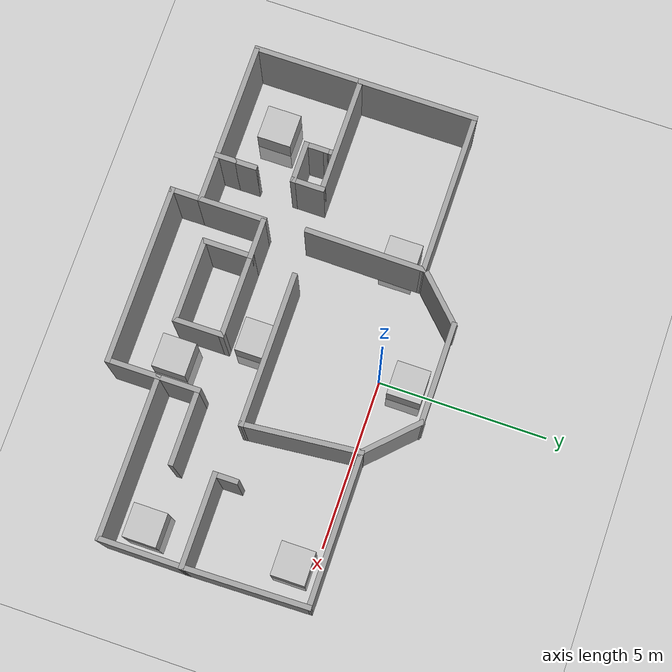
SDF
<sdf version="1.6">
 <world name="default">
  <light name="sun" type="directional">
   <pose>0 0 10 0 -0 0</pose>
   <diffuse>0.8 0.8 0.8 1</diffuse>
   <specular>0.2 0.2 0.2 1</specular>
   <attenuation>
    <range>1000</range>
    <constant>0.9</constant>
    <linear>0.01</linear>
    <quadratic>0.001</quadratic>
   </attenuation>
   <direction>-0.5 0.1 -0.9</direction>
  </light>
  <model name="ground_plane">
   <static>1</static>
   <link name="link">
    <collision name="collision">
     <geometry><plane><normal>0 0 1</normal><size>100 100</size></plane></geometry>
     <surface><friction><ode><mu>100</mu><mu2>50</mu2></ode></friction></surface>
    </collision>
    <visual name="visual">
     <cast_shadows>0</cast_shadows>
     <geometry><plane><normal>0 0 1</normal><size>100 100</size></plane></geometry>
     <material>
      <script><uri>file://media/materials/scripts/gazebo.material</uri><name>Gazebo/Grey</name></script>
     </material>
    </visual>
   </link>
  </model>
  <gravity>0 0 -9.8</gravity>
  <magnetic_field>6e-06 2.3e-05 -4.2e-05</magnetic_field>
  <atmosphere type="adiabatic"/>
  <physics name="default_physics" default="0" type="ode">
   <max_step_size>0.001</max_step_size>
   <real_time_factor>1</real_time_factor>
   <real_time_update_rate>1000</real_time_update_rate>
  </physics>
  <scene><ambient>0.4 0.4 0.4 1</ambient><background>0.7 0.7 0.7 1</background><shadows>1</shadows></scene>
  <spherical_coordinates>
   <surface_model>EARTH_WGS84</surface_model>
   <latitude_deg>0</latitude_deg>
   <longitude_deg>0</longitude_deg>
   <elevation>0</elevation>
   <heading_deg>0</heading_deg>
  </spherical_coordinates>
  <model name="box_contest3_clone_0">
   <link name="body">
    <inertial>
     <mass>1</mass>
     <inertia><ixx>1</ixx><ixy>0</ixy><ixz>0</ixz><iyy>1</iyy><iyz>0</iyz><izz>1</izz></inertia>
    </inertial>
    <visual name="visual">
     <geometry><mesh><uri>model://box_contest3.dae</uri><scale>1 1 1</scale></mesh></geometry>
     <material><shader type="vertex"><normal_map>__default__</normal_map></shader></material>
    </visual>
    <collision name="collision">
     <geometry><mesh><uri>__default__</uri><scale>1 1 1</scale></mesh></geometry>
     <surface>
      <friction>
       <ode><mu>1</mu><mu2>1</mu2><fdir1>0 0 0</fdir1><slip1>0</slip1><slip2>0</slip2></ode>
       <torsional>
        <coefficient>1</coefficient>
        <patch_radius>0</patch_radius>
        <surface_radius>0</surface_radius>
        <use_patch_radius>1</use_patch_radius>
        <ode><slip>0</slip></ode>
       </torsional>
      </friction>
      <bounce><restitution_coefficient>0</restitution_coefficient><threshold>1e+06</threshold></bounce>
      <contact>
       <collide_without_contact>0</collide_without_contact>
       <collide_without_contact_bitmask>1</collide_without_contact_bitmask>
       <collide_bitmask>1</collide_bitmask>
       <ode>
        <soft_cfm>0</soft_cfm>
        <soft_erp>0.2</soft_erp>
        <kp>1e+13</kp>
        <kd>1</kd>
        <max_vel>0.01</max_vel>
        <min_depth>0</min_depth>
       </ode>
       <bullet>
        <split_impulse>1</split_impulse>
        <split_impulse_penetration_threshold>-0.01</split_impulse_penetration_threshold>
        <soft_cfm>0</soft_cfm>
        <soft_erp>0.2</soft_erp>
        <kp>1e+13</kp>
        <kd>1</kd>
       </bullet>
      </contact>
     </surface>
    </collision>
   </link>
   <static>1</static>
   <pose>-0.13 0.83 -0.159 3.14159 -1.57079 3.14159</pose>
  </model>
  <model name="box_contest3_clone_1">
   <link name="body">
    <inertial>
     <mass>1</mass>
     <inertia><ixx>1</ixx><ixy>0</ixy><ixz>0</ixz><iyy>1</iyy><iyz>0</iyz><izz>1</izz></inertia>
    </inertial>
    <visual name="visual">
     <geometry><mesh><uri>model://box_contest3.dae</uri><scale>1 1 1</scale></mesh></geometry>
     <material><shader type="vertex"><normal_map>__default__</normal_map></shader></material>
    </visual>
    <collision name="collision">
     <geometry><mesh><uri>__default__</uri><scale>1 1 1</scale></mesh></geometry>
     <surface>
      <friction>
       <ode><mu>1</mu><mu2>1</mu2><fdir1>0 0 0</fdir1><slip1>0</slip1><slip2>0</slip2></ode>
       <torsional>
        <coefficient>1</coefficient>
        <patch_radius>0</patch_radius>
        <surface_radius>0</surface_radius>
        <use_patch_radius>1</use_patch_radius>
        <ode><slip>0</slip></ode>
       </torsional>
      </friction>
      <bounce><restitution_coefficient>0</restitution_coefficient><threshold>1e+06</threshold></bounce>
      <contact>
       <collide_without_contact>0</collide_without_contact>
       <collide_without_contact_bitmask>1</collide_without_contact_bitmask>
       <collide_bitmask>1</collide_bitmask>
       <ode>
        <soft_cfm>0</soft_cfm>
        <soft_erp>0.2</soft_erp>
        <kp>1e+13</kp>
        <kd>1</kd>
        <max_vel>0.01</max_vel>
        <min_depth>0</min_depth>
       </ode>
       <bullet>
        <split_impulse>1</split_impulse>
        <split_impulse_penetration_threshold>-0.01</split_impulse_penetration_threshold>
        <soft_cfm>0</soft_cfm>
        <soft_erp>0.2</soft_erp>
        <kp>1e+13</kp>
        <kd>1</kd>
       </bullet>
      </contact>
     </surface>
    </collision>
   </link>
   <static>1</static>
   <pose>-3.54 -0.52 -0.159 3.14159 -1.57079 3.14159</pose>
  </model>
  <model name="box_contest3_clone_2">
   <link name="body">
    <inertial>
     <mass>1</mass>
     <inertia><ixx>1</ixx><ixy>0</ixy><ixz>0</ixz><iyy>1</iyy><iyz>0</iyz><izz>1</izz></inertia>
    </inertial>
    <visual name="visual">
     <geometry><mesh><uri>model://box_contest3.dae</uri><scale>1 1 1</scale></mesh></geometry>
     <material><shader type="vertex"><normal_map>__default__</normal_map></shader></material>
    </visual>
    <collision name="collision">
     <geometry><mesh><uri>__default__</uri><scale>1 1 1</scale></mesh></geometry>
     <surface>
      <friction>
       <ode><mu>1</mu><mu2>1</mu2><fdir1>0 0 0</fdir1><slip1>0</slip1><slip2>0</slip2></ode>
       <torsional>
        <coefficient>1</coefficient>
        <patch_radius>0</patch_radius>
        <surface_radius>0</surface_radius>
        <use_patch_radius>1</use_patch_radius>
        <ode><slip>0</slip></ode>
       </torsional>
      </friction>
      <bounce><restitution_coefficient>0</restitution_coefficient><threshold>1e+06</threshold></bounce>
      <contact>
       <collide_without_contact>0</collide_without_contact>
       <collide_without_contact_bitmask>1</collide_without_contact_bitmask>
       <collide_bitmask>1</collide_bitmask>
       <ode>
        <soft_cfm>0</soft_cfm>
        <soft_erp>0.2</soft_erp>
        <kp>1e+13</kp>
        <kd>1</kd>
        <max_vel>0.01</max_vel>
        <min_depth>0</min_depth>
       </ode>
       <bullet>
        <split_impulse>1</split_impulse>
        <split_impulse_penetration_threshold>-0.01</split_impulse_penetration_threshold>
        <soft_cfm>0</soft_cfm>
        <soft_erp>0.2</soft_erp>
        <kp>1e+13</kp>
        <kd>1</kd>
       </bullet>
      </contact>
     </surface>
    </collision>
   </link>
   <static>1</static>
   <pose>-6.12 -5.12 -0.159 3.14159 -1.57079 3.14159</pose>
  </model>
  <model name="box_contest3_clone_3">
   <link name="body">
    <inertial>
     <mass>1</mass>
     <inertia><ixx>1</ixx><ixy>0</ixy><ixz>0</ixz><iyy>1</iyy><iyz>0</iyz><izz>1</izz></inertia>
    </inertial>
    <visual name="visual">
     <geometry><mesh><uri>model://box_contest3.dae</uri><scale>1 1 1</scale></mesh></geometry>
     <material><shader type="vertex"><normal_map>__default__</normal_map></shader></material>
    </visual>
    <collision name="collision">
     <geometry><mesh><uri>__default__</uri><scale>1 1 1</scale></mesh></geometry>
     <surface>
      <friction>
       <ode><mu>1</mu><mu2>1</mu2><fdir1>0 0 0</fdir1><slip1>0</slip1><slip2>0</slip2></ode>
       <torsional>
        <coefficient>1</coefficient>
        <patch_radius>0</patch_radius>
        <surface_radius>0</surface_radius>
        <use_patch_radius>1</use_patch_radius>
        <ode><slip>0</slip></ode>
       </torsional>
      </friction>
      <bounce><restitution_coefficient>0</restitution_coefficient><threshold>1e+06</threshold></bounce>
      <contact>
       <collide_without_contact>0</collide_without_contact>
       <collide_without_contact_bitmask>1</collide_without_contact_bitmask>
       <collide_bitmask>1</collide_bitmask>
       <ode>
        <soft_cfm>0</soft_cfm>
        <soft_erp>0.2</soft_erp>
        <kp>1e+13</kp>
        <kd>1</kd>
        <max_vel>0.01</max_vel>
        <min_depth>0</min_depth>
       </ode>
       <bullet>
        <split_impulse>1</split_impulse>
        <split_impulse_penetration_threshold>-0.01</split_impulse_penetration_threshold>
        <soft_cfm>0</soft_cfm>
        <soft_erp>0.2</soft_erp>
        <kp>1e+13</kp>
        <kd>1</kd>
       </bullet>
      </contact>
     </surface>
    </collision>
   </link>
   <static>1</static>
   <pose>1.24 -5.7 -0.159 3.14159 -1.57079 3.14159</pose>
  </model>
  <model name="box_contest3_clone_4">
   <link name="body">
    <inertial>
     <mass>1</mass>
     <inertia><ixx>1</ixx><ixy>0</ixy><ixz>0</ixz><iyy>1</iyy><iyz>0</iyz><izz>1</izz></inertia>
    </inertial>
    <visual name="visual">
     <geometry><mesh><uri>model://box_contest3.dae</uri><scale>1 1 1</scale></mesh></geometry>
     <material><shader type="vertex"><normal_map>__default__</normal_map></shader></material>
    </visual>
    <collision name="collision">
     <geometry><mesh><uri>__default__</uri><scale>1 1 1</scale></mesh></geometry>
     <surface>
      <friction>
       <ode><mu>1</mu><mu2>1</mu2><fdir1>0 0 0</fdir1><slip1>0</slip1><slip2>0</slip2></ode>
       <torsional>
        <coefficient>1</coefficient>
        <patch_radius>0</patch_radius>
        <surface_radius>0</surface_radius>
        <use_patch_radius>1</use_patch_radius>
        <ode><slip>0</slip></ode>
       </torsional>
      </friction>
      <bounce><restitution_coefficient>0</restitution_coefficient><threshold>1e+06</threshold></bounce>
      <contact>
       <collide_without_contact>0</collide_without_contact>
       <collide_without_contact_bitmask>1</collide_without_contact_bitmask>
       <collide_bitmask>1</collide_bitmask>
       <ode>
        <soft_cfm>0</soft_cfm>
        <soft_erp>0.2</soft_erp>
        <kp>1e+13</kp>
        <kd>1</kd>
        <max_vel>0.01</max_vel>
        <min_depth>0</min_depth>
       </ode>
       <bullet>
        <split_impulse>1</split_impulse>
        <split_impulse_penetration_threshold>-0.01</split_impulse_penetration_threshold>
        <soft_cfm>0</soft_cfm>
        <soft_erp>0.2</soft_erp>
        <kp>1e+13</kp>
        <kd>1</kd>
       </bullet>
      </contact>
     </surface>
    </collision>
   </link>
   <static>1</static>
   <pose>6.01 -4.82 -0.159 3.14159 -1.57079 3.14159</pose>
  </model>
  <model name="box_contest3_clone_5">
   <link name="body">
    <inertial>
     <mass>1</mass>
     <inertia><ixx>1</ixx><ixy>0</ixy><ixz>0</ixz><iyy>1</iyy><iyz>0</iyz><izz>1</izz></inertia>
    </inertial>
    <visual name="visual">
     <geometry><mesh><uri>model://box_contest3.dae</uri><scale>1 1 1</scale></mesh></geometry>
     <material><shader type="vertex"><normal_map>__default__</normal_map></shader></material>
    </visual>
    <collision name="collision">
     <geometry><mesh><uri>__default__</uri><scale>1 1 1</scale></mesh></geometry>
     <surface>
      <friction>
       <ode><mu>1</mu><mu2>1</mu2><fdir1>0 0 0</fdir1><slip1>0</slip1><slip2>0</slip2></ode>
       <torsional>
        <coefficient>1</coefficient>
        <patch_radius>0</patch_radius>
        <surface_radius>0</surface_radius>
        <use_patch_radius>1</use_patch_radius>
        <ode><slip>0</slip></ode>
       </torsional>
      </friction>
      <bounce><restitution_coefficient>0</restitution_coefficient><threshold>1e+06</threshold></bounce>
      <contact>
       <collide_without_contact>0</collide_without_contact>
       <collide_without_contact_bitmask>1</collide_without_contact_bitmask>
       <collide_bitmask>1</collide_bitmask>
       <ode>
        <soft_cfm>0</soft_cfm>
        <soft_erp>0.2</soft_erp>
        <kp>1e+13</kp>
        <kd>1</kd>
        <max_vel>0.01</max_vel>
        <min_depth>0</min_depth>
       </ode>
       <bullet>
        <split_impulse>1</split_impulse>
        <split_impulse_penetration_threshold>-0.01</split_impulse_penetration_threshold>
        <soft_cfm>0</soft_cfm>
        <soft_erp>0.2</soft_erp>
        <kp>1e+13</kp>
        <kd>1</kd>
       </bullet>
      </contact>
     </surface>
    </collision>
   </link>
   <static>1</static>
   <pose>5.69 -0.6 -0.159 3.14159 -1.57079 3.14159</pose>
  </model>
  <model name="box_contest3_clone_6">
   <link name="body">
    <inertial>
     <mass>1</mass>
     <inertia><ixx>1</ixx><ixy>0</ixy><ixz>0</ixz><iyy>1</iyy><iyz>0</iyz><izz>1</izz></inertia>
    </inertial>
    <visual name="visual">
     <geometry><mesh><uri>model://box_contest3.dae</uri><scale>1 1 1</scale></mesh></geometry>
     <material><shader type="vertex"><normal_map>__default__</normal_map></shader></material>
    </visual>
    <collision name="collision">
     <geometry><mesh><uri>__default__</uri><scale>1 1 1</scale></mesh></geometry>
     <surface>
      <friction>
       <ode><mu>1</mu><mu2>1</mu2><fdir1>0 0 0</fdir1><slip1>0</slip1><slip2>0</slip2></ode>
       <torsional>
        <coefficient>1</coefficient>
        <patch_radius>0</patch_radius>
        <surface_radius>0</surface_radius>
        <use_patch_radius>1</use_patch_radius>
        <ode><slip>0</slip></ode>
       </torsional>
      </friction>
      <bounce><restitution_coefficient>0</restitution_coefficient><threshold>1e+06</threshold></bounce>
      <contact>
       <collide_without_contact>0</collide_without_contact>
       <collide_without_contact_bitmask>1</collide_without_contact_bitmask>
       <collide_bitmask>1</collide_bitmask>
       <ode>
        <soft_cfm>0</soft_cfm>
        <soft_erp>0.2</soft_erp>
        <kp>1e+13</kp>
        <kd>1</kd>
        <max_vel>0.01</max_vel>
        <min_depth>0</min_depth>
       </ode>
       <bullet>
        <split_impulse>1</split_impulse>
        <split_impulse_penetration_threshold>-0.01</split_impulse_penetration_threshold>
        <soft_cfm>0</soft_cfm>
        <soft_erp>0.2</soft_erp>
        <kp>1e+13</kp>
        <kd>1</kd>
       </bullet>
      </contact>
     </surface>
    </collision>
   </link>
   <static>1</static>
   <pose>0.05 -3.64 -0.159 3.14159 -1.57079 3.14159</pose>
  </model>
  <model name="half-hexagon_0">
   <pose>-0.215109 0.880852 0 0 -0 0</pose>
   <link name="Wall_7">
    <collision name="Wall_7_Collision">
     <geometry><box><size>1.75 0.15 2.5</size></box></geometry>
     <pose>0 0 1.25 0 -0 0</pose>
    </collision>
    <visual name="Wall_7_Visual">
     <pose>0 0 1.25 0 -0 0</pose>
     <geometry><box><size>1.75 0.15 2.5</size></box></geometry>
     <material>
      <script><uri>file://media/materials/scripts/gazebo.material</uri><name>Gazebo/Grey</name></script>
      <ambient>1 1 1 1</ambient>
     </material>
    </visual>
    <pose>-2.07907 0.088388 0 0 -0 0.785398</pose>
   </link>
   <link name="Wall_8">
    <collision name="Wall_8_Collision">
     <geometry><box><size>3 0.15 2.5</size></box></geometry>
     <pose>0 0 1.25 0 -0 0</pose>
    </collision>
    <visual name="Wall_8_Visual">
     <pose>0 0 1.25 0 -0 0</pose>
     <geometry><box><size>3 0.15 2.5</size></box></geometry>
     <material>
      <script><uri>file://media/materials/scripts/gazebo.material</uri><name>Gazebo/Grey</name></script>
      <ambient>1 1 1 1</ambient>
     </material>
    </visual>
    <pose>-0.088388 0.654074 0 0 -0 0</pose>
   </link>
   <link name="Wall_9">
    <collision name="Wall_9_Collision">
     <geometry><box><size>2 0.15 2.5</size></box></geometry>
     <pose>0 0 1.25 0 -0 0</pose>
    </collision>
    <visual name="Wall_9_Visual">
     <pose>0 0 1.25 0 -0 0</pose>
     <geometry><box><size>2 0.15 2.5</size></box></geometry>
     <material>
      <script><uri>file://media/materials/scripts/gazebo.material</uri><name>Gazebo/Grey</name></script>
      <ambient>1 1 1 1</ambient>
     </material>
    </visual>
    <pose>1.99069 0 0 0 0 -0.785398</pose>
   </link>
   <static>1</static>
  </model>
  <model name="practicehouse">
   <link name="Wall_0">
    <pose>-7.20613 1.97161 0 0 0 -1.5708</pose>
    <visual name="Wall_0_Visual">
     <pose>0 0 1.25 0 -0 0</pose>
     <geometry><box><size>3.54 0.15 2.5</size></box></geometry>
     <material>
      <script><uri>file://media/materials/scripts/gazebo.material</uri><name>Gazebo/Grey</name></script>
      <ambient>1 1 1 1</ambient>
      <diffuse>0.7 0.7 0.7 1</diffuse>
      <specular>0.01 0.01 0.01 1</specular>
      <emissive>0 0 0 1</emissive>
     </material>
    </visual>
    <collision name="Wall_0_Collision">
     <pose>0 0 1.25 0 -0 0</pose>
     <geometry><box><size>3.54 0.15 2.5</size></box></geometry>
     <surface>
      <friction>
       <ode><mu>1</mu><mu2>1</mu2><fdir1>0 0 0</fdir1><slip1>0</slip1><slip2>0</slip2></ode>
       <torsional>
        <coefficient>1</coefficient>
        <patch_radius>0</patch_radius>
        <surface_radius>0</surface_radius>
        <use_patch_radius>1</use_patch_radius>
        <ode><slip>0</slip></ode>
       </torsional>
      </friction>
      <bounce><restitution_coefficient>0</restitution_coefficient><threshold>1e+06</threshold></bounce>
      <contact>
       <collide_without_contact>0</collide_without_contact>
       <collide_without_contact_bitmask>1</collide_without_contact_bitmask>
       <collide_bitmask>1</collide_bitmask>
       <ode>
        <soft_cfm>0</soft_cfm>
        <soft_erp>0.2</soft_erp>
        <kp>1e+13</kp>
        <kd>1</kd>
        <max_vel>0.01</max_vel>
        <min_depth>0</min_depth>
       </ode>
       <bullet>
        <split_impulse>1</split_impulse>
        <split_impulse_penetration_threshold>-0.01</split_impulse_penetration_threshold>
        <soft_cfm>0</soft_cfm>
        <soft_erp>0.2</soft_erp>
        <kp>1e+13</kp>
        <kd>1</kd>
       </bullet>
      </contact>
     </surface>
    </collision>
   </link>
   <link name="Wall_10">
    <pose>-4.95613 0.076607 0 0 -0 1.5708</pose>
    <visual name="Wall_10_Visual">
     <pose>0 0 1.25 0 -0 0</pose>
     <geometry><box><size>0.25 0.15 2.5</size></box></geometry>
     <material>
      <script><uri>file://media/materials/scripts/gazebo.material</uri><name>Gazebo/Grey</name></script>
      <ambient>1 1 1 1</ambient>
      <diffuse>0.7 0.7 0.7 1</diffuse>
      <specular>0.01 0.01 0.01 1</specular>
      <emissive>0 0 0 1</emissive>
     </material>
    </visual>
    <collision name="Wall_10_Collision">
     <pose>0 0 1.25 0 -0 0</pose>
     <geometry><box><size>0.25 0.15 2.5</size></box></geometry>
     <surface>
      <friction>
       <ode><mu>1</mu><mu2>1</mu2><fdir1>0 0 0</fdir1><slip1>0</slip1><slip2>0</slip2></ode>
       <torsional>
        <coefficient>1</coefficient>
        <patch_radius>0</patch_radius>
        <surface_radius>0</surface_radius>
        <use_patch_radius>1</use_patch_radius>
        <ode><slip>0</slip></ode>
       </torsional>
      </friction>
      <bounce><restitution_coefficient>0</restitution_coefficient><threshold>1e+06</threshold></bounce>
      <contact>
       <collide_without_contact>0</collide_without_contact>
       <collide_without_contact_bitmask>1</collide_without_contact_bitmask>
       <collide_bitmask>1</collide_bitmask>
       <ode>
        <soft_cfm>0</soft_cfm>
        <soft_erp>0.2</soft_erp>
        <kp>1e+13</kp>
        <kd>1</kd>
        <max_vel>0.01</max_vel>
        <min_depth>0</min_depth>
       </ode>
       <bullet>
        <split_impulse>1</split_impulse>
        <split_impulse_penetration_threshold>-0.01</split_impulse_penetration_threshold>
        <soft_cfm>0</soft_cfm>
        <soft_erp>0.2</soft_erp>
        <kp>1e+13</kp>
        <kd>1</kd>
       </bullet>
      </contact>
     </surface>
    </collision>
   </link>
   <link name="Wall_12">
    <pose>-7.20613 -1.27339 0 0 0 -1.5708</pose>
    <visual name="Wall_12_Visual">
     <pose>0 0 1.25 0 -0 0</pose>
     <geometry><box><size>3.25 0.15 2.5</size></box></geometry>
     <material>
      <script><uri>file://media/materials/scripts/gazebo.material</uri><name>Gazebo/Grey</name></script>
      <ambient>1 1 1 1</ambient>
      <diffuse>0.7 0.7 0.7 1</diffuse>
      <specular>0.01 0.01 0.01 1</specular>
      <emissive>0 0 0 1</emissive>
     </material>
    </visual>
    <collision name="Wall_12_Collision">
     <pose>0 0 1.25 0 -0 0</pose>
     <geometry><box><size>3.25 0.15 2.5</size></box></geometry>
     <surface>
      <friction>
       <ode><mu>1</mu><mu2>1</mu2><fdir1>0 0 0</fdir1><slip1>0</slip1><slip2>0</slip2></ode>
       <torsional>
        <coefficient>1</coefficient>
        <patch_radius>0</patch_radius>
        <surface_radius>0</surface_radius>
        <use_patch_radius>1</use_patch_radius>
        <ode><slip>0</slip></ode>
       </torsional>
      </friction>
      <bounce><restitution_coefficient>0</restitution_coefficient><threshold>1e+06</threshold></bounce>
      <contact>
       <collide_without_contact>0</collide_without_contact>
       <collide_without_contact_bitmask>1</collide_without_contact_bitmask>
       <collide_bitmask>1</collide_bitmask>
       <ode>
        <soft_cfm>0</soft_cfm>
        <soft_erp>0.2</soft_erp>
        <kp>1e+13</kp>
        <kd>1</kd>
        <max_vel>0.01</max_vel>
        <min_depth>0</min_depth>
       </ode>
       <bullet>
        <split_impulse>1</split_impulse>
        <split_impulse_penetration_threshold>-0.01</split_impulse_penetration_threshold>
        <soft_cfm>0</soft_cfm>
        <soft_erp>0.2</soft_erp>
        <kp>1e+13</kp>
        <kd>1</kd>
       </bullet>
      </contact>
     </surface>
    </collision>
   </link>
   <link name="Wall_13">
    <pose>-5.53113 -2.82339 0 0 -0 0</pose>
    <visual name="Wall_13_Visual">
     <pose>0 0 1.25 0 -0 0</pose>
     <geometry><box><size>3.5 0.15 2.5</size></box></geometry>
     <material>
      <script><uri>file://media/materials/scripts/gazebo.material</uri><name>Gazebo/Grey</name></script>
      <ambient>1 1 1 1</ambient>
      <diffuse>0.7 0.7 0.7 1</diffuse>
      <specular>0.01 0.01 0.01 1</specular>
      <emissive>0 0 0 1</emissive>
     </material>
    </visual>
    <collision name="Wall_13_Collision">
     <pose>0 0 1.25 0 -0 0</pose>
     <geometry><box><size>3.5 0.15 2.5</size></box></geometry>
     <surface>
      <friction>
       <ode><mu>1</mu><mu2>1</mu2><fdir1>0 0 0</fdir1><slip1>0</slip1><slip2>0</slip2></ode>
       <torsional>
        <coefficient>1</coefficient>
        <patch_radius>0</patch_radius>
        <surface_radius>0</surface_radius>
        <use_patch_radius>1</use_patch_radius>
        <ode><slip>0</slip></ode>
       </torsional>
      </friction>
      <bounce><restitution_coefficient>0</restitution_coefficient><threshold>1e+06</threshold></bounce>
      <contact>
       <collide_without_contact>0</collide_without_contact>
       <collide_without_contact_bitmask>1</collide_without_contact_bitmask>
       <collide_bitmask>1</collide_bitmask>
       <ode>
        <soft_cfm>0</soft_cfm>
        <soft_erp>0.2</soft_erp>
        <kp>1e+13</kp>
        <kd>1</kd>
        <max_vel>0.01</max_vel>
        <min_depth>0</min_depth>
       </ode>
       <bullet>
        <split_impulse>1</split_impulse>
        <split_impulse_penetration_threshold>-0.01</split_impulse_penetration_threshold>
        <soft_cfm>0</soft_cfm>
        <soft_erp>0.2</soft_erp>
        <kp>1e+13</kp>
        <kd>1</kd>
       </bullet>
      </contact>
     </surface>
    </collision>
   </link>
   <link name="Wall_14">
    <pose>-3.85613 -2.27339 0 0 -0 1.5708</pose>
    <visual name="Wall_14_Visual">
     <pose>0 0 1.25 0 -0 0</pose>
     <geometry><box><size>1.25 0.15 2.5</size></box></geometry>
     <material>
      <script><uri>file://media/materials/scripts/gazebo.material</uri><name>Gazebo/Grey</name></script>
      <ambient>1 1 1 1</ambient>
      <diffuse>0.7 0.7 0.7 1</diffuse>
      <specular>0.01 0.01 0.01 1</specular>
      <emissive>0 0 0 1</emissive>
     </material>
    </visual>
    <collision name="Wall_14_Collision">
     <pose>0 0 1.25 0 -0 0</pose>
     <geometry><box><size>1.25 0.15 2.5</size></box></geometry>
     <surface>
      <friction>
       <ode><mu>1</mu><mu2>1</mu2><fdir1>0 0 0</fdir1><slip1>0</slip1><slip2>0</slip2></ode>
       <torsional>
        <coefficient>1</coefficient>
        <patch_radius>0</patch_radius>
        <surface_radius>0</surface_radius>
        <use_patch_radius>1</use_patch_radius>
        <ode><slip>0</slip></ode>
       </torsional>
      </friction>
      <bounce><restitution_coefficient>0</restitution_coefficient><threshold>1e+06</threshold></bounce>
      <contact>
       <collide_without_contact>0</collide_without_contact>
       <collide_without_contact_bitmask>1</collide_without_contact_bitmask>
       <collide_bitmask>1</collide_bitmask>
       <ode>
        <soft_cfm>0</soft_cfm>
        <soft_erp>0.2</soft_erp>
        <kp>1e+13</kp>
        <kd>1</kd>
        <max_vel>0.01</max_vel>
        <min_depth>0</min_depth>
       </ode>
       <bullet>
        <split_impulse>1</split_impulse>
        <split_impulse_penetration_threshold>-0.01</split_impulse_penetration_threshold>
        <soft_cfm>0</soft_cfm>
        <soft_erp>0.2</soft_erp>
        <kp>1e+13</kp>
        <kd>1</kd>
       </bullet>
      </contact>
     </surface>
    </collision>
   </link>
   <link name="Wall_15">
    <pose>-3.85613 -2.27339 0 0 0 -1.5708</pose>
    <visual name="Wall_15_Visual">
     <pose>0 0 1.25 0 -0 0</pose>
     <geometry><box><size>1.25 0.15 2.5</size></box></geometry>
     <material>
      <script><uri>file://media/materials/scripts/gazebo.material</uri><name>Gazebo/Grey</name></script>
      <ambient>1 1 1 1</ambient>
      <diffuse>0.7 0.7 0.7 1</diffuse>
      <specular>0.01 0.01 0.01 1</specular>
      <emissive>0 0 0 1</emissive>
     </material>
    </visual>
    <collision name="Wall_15_Collision">
     <pose>0 0 1.25 0 -0 0</pose>
     <geometry><box><size>1.25 0.15 2.5</size></box></geometry>
     <surface>
      <friction>
       <ode><mu>1</mu><mu2>1</mu2><fdir1>0 0 0</fdir1><slip1>0</slip1><slip2>0</slip2></ode>
       <torsional>
        <coefficient>1</coefficient>
        <patch_radius>0</patch_radius>
        <surface_radius>0</surface_radius>
        <use_patch_radius>1</use_patch_radius>
        <ode><slip>0</slip></ode>
       </torsional>
      </friction>
      <bounce><restitution_coefficient>0</restitution_coefficient><threshold>1e+06</threshold></bounce>
      <contact>
       <collide_without_contact>0</collide_without_contact>
       <collide_without_contact_bitmask>1</collide_without_contact_bitmask>
       <collide_bitmask>1</collide_bitmask>
       <ode>
        <soft_cfm>0</soft_cfm>
        <soft_erp>0.2</soft_erp>
        <kp>1e+13</kp>
        <kd>1</kd>
        <max_vel>0.01</max_vel>
        <min_depth>0</min_depth>
       </ode>
       <bullet>
        <split_impulse>1</split_impulse>
        <split_impulse_penetration_threshold>-0.01</split_impulse_penetration_threshold>
        <soft_cfm>0</soft_cfm>
        <soft_erp>0.2</soft_erp>
        <kp>1e+13</kp>
        <kd>1</kd>
       </bullet>
      </contact>
     </surface>
    </collision>
   </link>
   <link name="Wall_16">
    <pose>-3.18113 -2.82339 0 0 -0 0</pose>
    <visual name="Wall_16_Visual">
     <pose>0 0 1.25 0 -0 0</pose>
     <geometry><box><size>1.5 0.15 2.5</size></box></geometry>
     <material>
      <script><uri>file://media/materials/scripts/gazebo.material</uri><name>Gazebo/Grey</name></script>
      <ambient>1 1 1 1</ambient>
      <diffuse>0.7 0.7 0.7 1</diffuse>
      <specular>0.01 0.01 0.01 1</specular>
      <emissive>0 0 0 1</emissive>
     </material>
    </visual>
    <collision name="Wall_16_Collision">
     <pose>0 0 1.25 0 -0 0</pose>
     <geometry><box><size>1.5 0.15 2.5</size></box></geometry>
     <surface>
      <friction>
       <ode><mu>1</mu><mu2>1</mu2><fdir1>0 0 0</fdir1><slip1>0</slip1><slip2>0</slip2></ode>
       <torsional>
        <coefficient>1</coefficient>
        <patch_radius>0</patch_radius>
        <surface_radius>0</surface_radius>
        <use_patch_radius>1</use_patch_radius>
        <ode><slip>0</slip></ode>
       </torsional>
      </friction>
      <bounce><restitution_coefficient>0</restitution_coefficient><threshold>1e+06</threshold></bounce>
      <contact>
       <collide_without_contact>0</collide_without_contact>
       <collide_without_contact_bitmask>1</collide_without_contact_bitmask>
       <collide_bitmask>1</collide_bitmask>
       <ode>
        <soft_cfm>0</soft_cfm>
        <soft_erp>0.2</soft_erp>
        <kp>1e+13</kp>
        <kd>1</kd>
        <max_vel>0.01</max_vel>
        <min_depth>0</min_depth>
       </ode>
       <bullet>
        <split_impulse>1</split_impulse>
        <split_impulse_penetration_threshold>-0.01</split_impulse_penetration_threshold>
        <soft_cfm>0</soft_cfm>
        <soft_erp>0.2</soft_erp>
        <kp>1e+13</kp>
        <kd>1</kd>
       </bullet>
      </contact>
     </surface>
    </collision>
   </link>
   <link name="Wall_17">
    <pose>-2.50613 -1.89839 0 0 -0 1.5708</pose>
    <visual name="Wall_17_Visual">
     <pose>0 0 1.25 0 -0 0</pose>
     <geometry><box><size>2 0.15 2.5</size></box></geometry>
     <material>
      <script><uri>file://media/materials/scripts/gazebo.material</uri><name>Gazebo/Grey</name></script>
      <ambient>1 1 1 1</ambient>
      <diffuse>0.7 0.7 0.7 1</diffuse>
      <specular>0.01 0.01 0.01 1</specular>
      <emissive>0 0 0 1</emissive>
     </material>
    </visual>
    <collision name="Wall_17_Collision">
     <pose>0 0 1.25 0 -0 0</pose>
     <geometry><box><size>2 0.15 2.5</size></box></geometry>
     <surface>
      <friction>
       <ode><mu>1</mu><mu2>1</mu2><fdir1>0 0 0</fdir1><slip1>0</slip1><slip2>0</slip2></ode>
       <torsional>
        <coefficient>1</coefficient>
        <patch_radius>0</patch_radius>
        <surface_radius>0</surface_radius>
        <use_patch_radius>1</use_patch_radius>
        <ode><slip>0</slip></ode>
       </torsional>
      </friction>
      <bounce><restitution_coefficient>0</restitution_coefficient><threshold>1e+06</threshold></bounce>
      <contact>
       <collide_without_contact>0</collide_without_contact>
       <collide_without_contact_bitmask>1</collide_without_contact_bitmask>
       <collide_bitmask>1</collide_bitmask>
       <ode>
        <soft_cfm>0</soft_cfm>
        <soft_erp>0.2</soft_erp>
        <kp>1e+13</kp>
        <kd>1</kd>
        <max_vel>0.01</max_vel>
        <min_depth>0</min_depth>
       </ode>
       <bullet>
        <split_impulse>1</split_impulse>
        <split_impulse_penetration_threshold>-0.01</split_impulse_penetration_threshold>
        <soft_cfm>0</soft_cfm>
        <soft_erp>0.2</soft_erp>
        <kp>1e+13</kp>
        <kd>1</kd>
       </bullet>
      </contact>
     </surface>
    </collision>
   </link>
   <link name="Wall_18">
    <pose>-1.95613 -0.973393 0 0 -0 0</pose>
    <visual name="Wall_18_Visual">
     <pose>0 0 1.25 0 -0 0</pose>
     <geometry><box><size>1.25 0.15 2.5</size></box></geometry>
     <material>
      <script><uri>file://media/materials/scripts/gazebo.material</uri><name>Gazebo/Grey</name></script>
      <ambient>1 1 1 1</ambient>
      <diffuse>0.7 0.7 0.7 1</diffuse>
      <specular>0.01 0.01 0.01 1</specular>
      <emissive>0 0 0 1</emissive>
     </material>
    </visual>
    <collision name="Wall_18_Collision">
     <pose>0 0 1.25 0 -0 0</pose>
     <geometry><box><size>1.25 0.15 2.5</size></box></geometry>
     <surface>
      <friction>
       <ode><mu>1</mu><mu2>1</mu2><fdir1>0 0 0</fdir1><slip1>0</slip1><slip2>0</slip2></ode>
       <torsional>
        <coefficient>1</coefficient>
        <patch_radius>0</patch_radius>
        <surface_radius>0</surface_radius>
        <use_patch_radius>1</use_patch_radius>
        <ode><slip>0</slip></ode>
       </torsional>
      </friction>
      <bounce><restitution_coefficient>0</restitution_coefficient><threshold>1e+06</threshold></bounce>
      <contact>
       <collide_without_contact>0</collide_without_contact>
       <collide_without_contact_bitmask>1</collide_without_contact_bitmask>
       <collide_bitmask>1</collide_bitmask>
       <ode>
        <soft_cfm>0</soft_cfm>
        <soft_erp>0.2</soft_erp>
        <kp>1e+13</kp>
        <kd>1</kd>
        <max_vel>0.01</max_vel>
        <min_depth>0</min_depth>
       </ode>
       <bullet>
        <split_impulse>1</split_impulse>
        <split_impulse_penetration_threshold>-0.01</split_impulse_penetration_threshold>
        <soft_cfm>0</soft_cfm>
        <soft_erp>0.2</soft_erp>
        <kp>1e+13</kp>
        <kd>1</kd>
       </bullet>
      </contact>
     </surface>
    </collision>
   </link>
   <link name="Wall_19">
    <pose>-1.40613 -1.64839 0 0 0 -1.5708</pose>
    <visual name="Wall_19_Visual">
     <pose>0 0 1.25 0 -0 0</pose>
     <geometry><box><size>1.5 0.15 2.5</size></box></geometry>
     <material>
      <script><uri>file://media/materials/scripts/gazebo.material</uri><name>Gazebo/Grey</name></script>
      <ambient>1 1 1 1</ambient>
      <diffuse>0.7 0.7 0.7 1</diffuse>
      <specular>0.01 0.01 0.01 1</specular>
      <emissive>0 0 0 1</emissive>
     </material>
    </visual>
    <collision name="Wall_19_Collision">
     <pose>0 0 1.25 0 -0 0</pose>
     <geometry><box><size>1.5 0.15 2.5</size></box></geometry>
     <surface>
      <friction>
       <ode><mu>1</mu><mu2>1</mu2><fdir1>0 0 0</fdir1><slip1>0</slip1><slip2>0</slip2></ode>
       <torsional>
        <coefficient>1</coefficient>
        <patch_radius>0</patch_radius>
        <surface_radius>0</surface_radius>
        <use_patch_radius>1</use_patch_radius>
        <ode><slip>0</slip></ode>
       </torsional>
      </friction>
      <bounce><restitution_coefficient>0</restitution_coefficient><threshold>1e+06</threshold></bounce>
      <contact>
       <collide_without_contact>0</collide_without_contact>
       <collide_without_contact_bitmask>1</collide_without_contact_bitmask>
       <collide_bitmask>1</collide_bitmask>
       <ode>
        <soft_cfm>0</soft_cfm>
        <soft_erp>0.2</soft_erp>
        <kp>1e+13</kp>
        <kd>1</kd>
        <max_vel>0.01</max_vel>
        <min_depth>0</min_depth>
       </ode>
       <bullet>
        <split_impulse>1</split_impulse>
        <split_impulse_penetration_threshold>-0.01</split_impulse_penetration_threshold>
        <soft_cfm>0</soft_cfm>
        <soft_erp>0.2</soft_erp>
        <kp>1e+13</kp>
        <kd>1</kd>
       </bullet>
      </contact>
     </surface>
    </collision>
   </link>
   <link name="Wall_2">
    <pose>-4.88863 3.66661 0 0 -0 0</pose>
    <visual name="Wall_2_Visual">
     <pose>0 0 1.25 0 -0 0</pose>
     <geometry><box><size>4.78498 0.15 2.5</size></box></geometry>
     <material>
      <script><uri>file://media/materials/scripts/gazebo.material</uri><name>Gazebo/Grey</name></script>
      <ambient>1 1 1 1</ambient>
      <diffuse>0.7 0.7 0.7 1</diffuse>
      <specular>0.01 0.01 0.01 1</specular>
      <emissive>0 0 0 1</emissive>
     </material>
    </visual>
    <collision name="Wall_2_Collision">
     <pose>0 0 1.25 0 -0 0</pose>
     <geometry><box><size>4.78498 0.15 2.5</size></box></geometry>
     <surface>
      <friction>
       <ode><mu>1</mu><mu2>1</mu2><fdir1>0 0 0</fdir1><slip1>0</slip1><slip2>0</slip2></ode>
       <torsional>
        <coefficient>1</coefficient>
        <patch_radius>0</patch_radius>
        <surface_radius>0</surface_radius>
        <use_patch_radius>1</use_patch_radius>
        <ode><slip>0</slip></ode>
       </torsional>
      </friction>
      <bounce><restitution_coefficient>0</restitution_coefficient><threshold>1e+06</threshold></bounce>
      <contact>
       <collide_without_contact>0</collide_without_contact>
       <collide_without_contact_bitmask>1</collide_without_contact_bitmask>
       <collide_bitmask>1</collide_bitmask>
       <ode>
        <soft_cfm>0</soft_cfm>
        <soft_erp>0.2</soft_erp>
        <kp>1e+13</kp>
        <kd>1</kd>
        <max_vel>0.01</max_vel>
        <min_depth>0</min_depth>
       </ode>
       <bullet>
        <split_impulse>1</split_impulse>
        <split_impulse_penetration_threshold>-0.01</split_impulse_penetration_threshold>
        <soft_cfm>0</soft_cfm>
        <soft_erp>0.2</soft_erp>
        <kp>1e+13</kp>
        <kd>1</kd>
       </bullet>
      </contact>
     </surface>
    </collision>
   </link>
   <link name="Wall_20">
    <pose>-0.231133 -2.32339 0 0 -0 0</pose>
    <visual name="Wall_20_Visual">
     <pose>0 0 1.25 0 -0 0</pose>
     <geometry><box><size>2.5 0.15 2.5</size></box></geometry>
     <material>
      <script><uri>file://media/materials/scripts/gazebo.material</uri><name>Gazebo/Grey</name></script>
      <ambient>1 1 1 1</ambient>
      <diffuse>0.7 0.7 0.7 1</diffuse>
      <specular>0.01 0.01 0.01 1</specular>
      <emissive>0 0 0 1</emissive>
     </material>
    </visual>
    <collision name="Wall_20_Collision">
     <pose>0 0 1.25 0 -0 0</pose>
     <geometry><box><size>2.5 0.15 2.5</size></box></geometry>
     <surface>
      <friction>
       <ode><mu>1</mu><mu2>1</mu2><fdir1>0 0 0</fdir1><slip1>0</slip1><slip2>0</slip2></ode>
       <torsional>
        <coefficient>1</coefficient>
        <patch_radius>0</patch_radius>
        <surface_radius>0</surface_radius>
        <use_patch_radius>1</use_patch_radius>
        <ode><slip>0</slip></ode>
       </torsional>
      </friction>
      <bounce><restitution_coefficient>0</restitution_coefficient><threshold>1e+06</threshold></bounce>
      <contact>
       <collide_without_contact>0</collide_without_contact>
       <collide_without_contact_bitmask>1</collide_without_contact_bitmask>
       <collide_bitmask>1</collide_bitmask>
       <ode>
        <soft_cfm>0</soft_cfm>
        <soft_erp>0.2</soft_erp>
        <kp>1e+13</kp>
        <kd>1</kd>
        <max_vel>0.01</max_vel>
        <min_depth>0</min_depth>
       </ode>
       <bullet>
        <split_impulse>1</split_impulse>
        <split_impulse_penetration_threshold>-0.01</split_impulse_penetration_threshold>
        <soft_cfm>0</soft_cfm>
        <soft_erp>0.2</soft_erp>
        <kp>1e+13</kp>
        <kd>1</kd>
       </bullet>
      </contact>
     </surface>
    </collision>
   </link>
   <link name="Wall_21">
    <pose>0.943867 -1.64839 0 0 -0 1.5708</pose>
    <visual name="Wall_21_Visual">
     <pose>0 0 1.25 0 -0 0</pose>
     <geometry><box><size>1.5 0.15 2.5</size></box></geometry>
     <material>
      <script><uri>file://media/materials/scripts/gazebo.material</uri><name>Gazebo/Grey</name></script>
      <ambient>1 1 1 1</ambient>
      <diffuse>0.7 0.7 0.7 1</diffuse>
      <specular>0.01 0.01 0.01 1</specular>
      <emissive>0 0 0 1</emissive>
     </material>
    </visual>
    <collision name="Wall_21_Collision">
     <pose>0 0 1.25 0 -0 0</pose>
     <geometry><box><size>1.5 0.15 2.5</size></box></geometry>
     <surface>
      <friction>
       <ode><mu>1</mu><mu2>1</mu2><fdir1>0 0 0</fdir1><slip1>0</slip1><slip2>0</slip2></ode>
       <torsional>
        <coefficient>1</coefficient>
        <patch_radius>0</patch_radius>
        <surface_radius>0</surface_radius>
        <use_patch_radius>1</use_patch_radius>
        <ode><slip>0</slip></ode>
       </torsional>
      </friction>
      <bounce><restitution_coefficient>0</restitution_coefficient><threshold>1e+06</threshold></bounce>
      <contact>
       <collide_without_contact>0</collide_without_contact>
       <collide_without_contact_bitmask>1</collide_without_contact_bitmask>
       <collide_bitmask>1</collide_bitmask>
       <ode>
        <soft_cfm>0</soft_cfm>
        <soft_erp>0.2</soft_erp>
        <kp>1e+13</kp>
        <kd>1</kd>
        <max_vel>0.01</max_vel>
        <min_depth>0</min_depth>
       </ode>
       <bullet>
        <split_impulse>1</split_impulse>
        <split_impulse_penetration_threshold>-0.01</split_impulse_penetration_threshold>
        <soft_cfm>0</soft_cfm>
        <soft_erp>0.2</soft_erp>
        <kp>1e+13</kp>
        <kd>1</kd>
       </bullet>
      </contact>
     </surface>
    </collision>
   </link>
   <link name="Wall_22">
    <pose>-0.231133 -0.973393 0 0 -0 3.14159</pose>
    <visual name="Wall_22_Visual">
     <pose>0 0 1.25 0 -0 0</pose>
     <geometry><box><size>2.5 0.15 2.5</size></box></geometry>
     <material>
      <script><uri>file://media/materials/scripts/gazebo.material</uri><name>Gazebo/Grey</name></script>
      <ambient>1 1 1 1</ambient>
      <diffuse>0.7 0.7 0.7 1</diffuse>
      <specular>0.01 0.01 0.01 1</specular>
      <emissive>0 0 0 1</emissive>
     </material>
    </visual>
    <collision name="Wall_22_Collision">
     <pose>0 0 1.25 0 -0 0</pose>
     <geometry><box><size>2.5 0.15 2.5</size></box></geometry>
     <surface>
      <friction>
       <ode><mu>1</mu><mu2>1</mu2><fdir1>0 0 0</fdir1><slip1>0</slip1><slip2>0</slip2></ode>
       <torsional>
        <coefficient>1</coefficient>
        <patch_radius>0</patch_radius>
        <surface_radius>0</surface_radius>
        <use_patch_radius>1</use_patch_radius>
        <ode><slip>0</slip></ode>
       </torsional>
      </friction>
      <bounce><restitution_coefficient>0</restitution_coefficient><threshold>1e+06</threshold></bounce>
      <contact>
       <collide_without_contact>0</collide_without_contact>
       <collide_without_contact_bitmask>1</collide_without_contact_bitmask>
       <collide_bitmask>1</collide_bitmask>
       <ode>
        <soft_cfm>0</soft_cfm>
        <soft_erp>0.2</soft_erp>
        <kp>1e+13</kp>
        <kd>1</kd>
        <max_vel>0.01</max_vel>
        <min_depth>0</min_depth>
       </ode>
       <bullet>
        <split_impulse>1</split_impulse>
        <split_impulse_penetration_threshold>-0.01</split_impulse_penetration_threshold>
        <soft_cfm>0</soft_cfm>
        <soft_erp>0.2</soft_erp>
        <kp>1e+13</kp>
        <kd>1</kd>
       </bullet>
      </contact>
     </surface>
    </collision>
   </link>
   <link name="Wall_24">
    <pose>-2.50613 -3.24839 0 0 0 -1.5708</pose>
    <visual name="Wall_24_Visual">
     <pose>0 0 1.25 0 -0 0</pose>
     <geometry><box><size>1 0.15 2.5</size></box></geometry>
     <material>
      <script><uri>file://media/materials/scripts/gazebo.material</uri><name>Gazebo/Grey</name></script>
      <ambient>1 1 1 1</ambient>
      <diffuse>0.7 0.7 0.7 1</diffuse>
      <specular>0.01 0.01 0.01 1</specular>
      <emissive>0 0 0 1</emissive>
     </material>
    </visual>
    <collision name="Wall_24_Collision">
     <pose>0 0 1.25 0 -0 0</pose>
     <geometry><box><size>1 0.15 2.5</size></box></geometry>
     <surface>
      <friction>
       <ode><mu>1</mu><mu2>1</mu2><fdir1>0 0 0</fdir1><slip1>0</slip1><slip2>0</slip2></ode>
       <torsional>
        <coefficient>1</coefficient>
        <patch_radius>0</patch_radius>
        <surface_radius>0</surface_radius>
        <use_patch_radius>1</use_patch_radius>
        <ode><slip>0</slip></ode>
       </torsional>
      </friction>
      <bounce><restitution_coefficient>0</restitution_coefficient><threshold>1e+06</threshold></bounce>
      <contact>
       <collide_without_contact>0</collide_without_contact>
       <collide_without_contact_bitmask>1</collide_without_contact_bitmask>
       <collide_bitmask>1</collide_bitmask>
       <ode>
        <soft_cfm>0</soft_cfm>
        <soft_erp>0.2</soft_erp>
        <kp>1e+13</kp>
        <kd>1</kd>
        <max_vel>0.01</max_vel>
        <min_depth>0</min_depth>
       </ode>
       <bullet>
        <split_impulse>1</split_impulse>
        <split_impulse_penetration_threshold>-0.01</split_impulse_penetration_threshold>
        <soft_cfm>0</soft_cfm>
        <soft_erp>0.2</soft_erp>
        <kp>1e+13</kp>
        <kd>1</kd>
       </bullet>
      </contact>
     </surface>
    </collision>
   </link>
   <link name="Wall_25">
    <pose>0.043867 -3.67339 0 0 -0 0</pose>
    <visual name="Wall_25_Visual">
     <pose>0 0 1.25 0 -0 0</pose>
     <geometry><box><size>5.25 0.15 2.5</size></box></geometry>
     <material>
      <script><uri>file://media/materials/scripts/gazebo.material</uri><name>Gazebo/Grey</name></script>
      <ambient>1 1 1 1</ambient>
      <diffuse>0.7 0.7 0.7 1</diffuse>
      <specular>0.01 0.01 0.01 1</specular>
      <emissive>0 0 0 1</emissive>
     </material>
    </visual>
    <collision name="Wall_25_Collision">
     <pose>0 0 1.25 0 -0 0</pose>
     <geometry><box><size>5.25 0.15 2.5</size></box></geometry>
     <surface>
      <friction>
       <ode><mu>1</mu><mu2>1</mu2><fdir1>0 0 0</fdir1><slip1>0</slip1><slip2>0</slip2></ode>
       <torsional>
        <coefficient>1</coefficient>
        <patch_radius>0</patch_radius>
        <surface_radius>0</surface_radius>
        <use_patch_radius>1</use_patch_radius>
        <ode><slip>0</slip></ode>
       </torsional>
      </friction>
      <bounce><restitution_coefficient>0</restitution_coefficient><threshold>1e+06</threshold></bounce>
      <contact>
       <collide_without_contact>0</collide_without_contact>
       <collide_without_contact_bitmask>1</collide_without_contact_bitmask>
       <collide_bitmask>1</collide_bitmask>
       <ode>
        <soft_cfm>0</soft_cfm>
        <soft_erp>0.2</soft_erp>
        <kp>1e+13</kp>
        <kd>1</kd>
        <max_vel>0.01</max_vel>
        <min_depth>0</min_depth>
       </ode>
       <bullet>
        <split_impulse>1</split_impulse>
        <split_impulse_penetration_threshold>-0.01</split_impulse_penetration_threshold>
        <soft_cfm>0</soft_cfm>
        <soft_erp>0.2</soft_erp>
        <kp>1e+13</kp>
        <kd>1</kd>
       </bullet>
      </contact>
     </surface>
    </collision>
   </link>
   <link name="Wall_26">
    <pose>2.59387 -2.37339 0 0 -0 1.5708</pose>
    <visual name="Wall_26_Visual">
     <pose>0 0 1.25 0 -0 0</pose>
     <geometry><box><size>2.75 0.15 2.5</size></box></geometry>
     <material>
      <script><uri>file://media/materials/scripts/gazebo.material</uri><name>Gazebo/Grey</name></script>
      <ambient>1 1 1 1</ambient>
      <diffuse>0.7 0.7 0.7 1</diffuse>
      <specular>0.01 0.01 0.01 1</specular>
      <emissive>0 0 0 1</emissive>
     </material>
    </visual>
    <collision name="Wall_26_Collision">
     <pose>0 0 1.25 0 -0 0</pose>
     <geometry><box><size>2.75 0.15 2.5</size></box></geometry>
     <surface>
      <friction>
       <ode><mu>1</mu><mu2>1</mu2><fdir1>0 0 0</fdir1><slip1>0</slip1><slip2>0</slip2></ode>
       <torsional>
        <coefficient>1</coefficient>
        <patch_radius>0</patch_radius>
        <surface_radius>0</surface_radius>
        <use_patch_radius>1</use_patch_radius>
        <ode><slip>0</slip></ode>
       </torsional>
      </friction>
      <bounce><restitution_coefficient>0</restitution_coefficient><threshold>1e+06</threshold></bounce>
      <contact>
       <collide_without_contact>0</collide_without_contact>
       <collide_without_contact_bitmask>1</collide_without_contact_bitmask>
       <collide_bitmask>1</collide_bitmask>
       <ode>
        <soft_cfm>0</soft_cfm>
        <soft_erp>0.2</soft_erp>
        <kp>1e+13</kp>
        <kd>1</kd>
        <max_vel>0.01</max_vel>
        <min_depth>0</min_depth>
       </ode>
       <bullet>
        <split_impulse>1</split_impulse>
        <split_impulse_penetration_threshold>-0.01</split_impulse_penetration_threshold>
        <soft_cfm>0</soft_cfm>
        <soft_erp>0.2</soft_erp>
        <kp>1e+13</kp>
        <kd>1</kd>
       </bullet>
      </contact>
     </surface>
    </collision>
   </link>
   <link name="Wall_27">
    <pose>3.64387 -1.07339 0 0 -0 0</pose>
    <visual name="Wall_27_Visual">
     <pose>0 0 1.25 0 -0 0</pose>
     <geometry><box><size>2.25 0.15 2.5</size></box></geometry>
     <material>
      <script><uri>file://media/materials/scripts/gazebo.material</uri><name>Gazebo/Grey</name></script>
      <ambient>1 1 1 1</ambient>
      <diffuse>0.7 0.7 0.7 1</diffuse>
      <specular>0.01 0.01 0.01 1</specular>
      <emissive>0 0 0 1</emissive>
     </material>
    </visual>
    <collision name="Wall_27_Collision">
     <pose>0 0 1.25 0 -0 0</pose>
     <geometry><box><size>2.25 0.15 2.5</size></box></geometry>
     <surface>
      <friction>
       <ode><mu>1</mu><mu2>1</mu2><fdir1>0 0 0</fdir1><slip1>0</slip1><slip2>0</slip2></ode>
       <torsional>
        <coefficient>1</coefficient>
        <patch_radius>0</patch_radius>
        <surface_radius>0</surface_radius>
        <use_patch_radius>1</use_patch_radius>
        <ode><slip>0</slip></ode>
       </torsional>
      </friction>
      <bounce><restitution_coefficient>0</restitution_coefficient><threshold>1e+06</threshold></bounce>
      <contact>
       <collide_without_contact>0</collide_without_contact>
       <collide_without_contact_bitmask>1</collide_without_contact_bitmask>
       <collide_bitmask>1</collide_bitmask>
       <ode>
        <soft_cfm>0</soft_cfm>
        <soft_erp>0.2</soft_erp>
        <kp>1e+13</kp>
        <kd>1</kd>
        <max_vel>0.01</max_vel>
        <min_depth>0</min_depth>
       </ode>
       <bullet>
        <split_impulse>1</split_impulse>
        <split_impulse_penetration_threshold>-0.01</split_impulse_penetration_threshold>
        <soft_cfm>0</soft_cfm>
        <soft_erp>0.2</soft_erp>
        <kp>1e+13</kp>
        <kd>1</kd>
       </bullet>
      </contact>
     </surface>
    </collision>
   </link>
   <link name="Wall_29">
    <pose>4.90454 -2.21861 0 0 -0 0</pose>
    <visual name="Wall_29_Visual">
     <pose>0 0 1.25 0 -0 0</pose>
     <geometry><box><size>4.75 0.15 2.5</size></box></geometry>
     <material>
      <script><uri>file://media/materials/scripts/gazebo.material</uri><name>Gazebo/Grey</name></script>
      <ambient>1 1 1 1</ambient>
      <diffuse>0.7 0.7 0.7 1</diffuse>
      <specular>0.01 0.01 0.01 1</specular>
      <emissive>0 0 0 1</emissive>
     </material>
    </visual>
    <collision name="Wall_29_Collision">
     <pose>0 0 1.25 0 -0 0</pose>
     <geometry><box><size>4.75 0.15 2.5</size></box></geometry>
     <surface>
      <friction>
       <ode><mu>1</mu><mu2>1</mu2><fdir1>0 0 0</fdir1><slip1>0</slip1><slip2>0</slip2></ode>
       <torsional>
        <coefficient>1</coefficient>
        <patch_radius>0</patch_radius>
        <surface_radius>0</surface_radius>
        <use_patch_radius>1</use_patch_radius>
        <ode><slip>0</slip></ode>
       </torsional>
      </friction>
      <bounce><restitution_coefficient>0</restitution_coefficient><threshold>1e+06</threshold></bounce>
      <contact>
       <collide_without_contact>0</collide_without_contact>
       <collide_without_contact_bitmask>1</collide_without_contact_bitmask>
       <collide_bitmask>1</collide_bitmask>
       <ode>
        <soft_cfm>0</soft_cfm>
        <soft_erp>0.2</soft_erp>
        <kp>1e+13</kp>
        <kd>1</kd>
        <max_vel>0.01</max_vel>
        <min_depth>0</min_depth>
       </ode>
       <bullet>
        <split_impulse>1</split_impulse>
        <split_impulse_penetration_threshold>-0.01</split_impulse_penetration_threshold>
        <soft_cfm>0</soft_cfm>
        <soft_erp>0.2</soft_erp>
        <kp>1e+13</kp>
        <kd>1</kd>
       </bullet>
      </contact>
     </surface>
    </collision>
   </link>
   <link name="Wall_3">
    <pose>-2.58863 1.97161 0 0 0 -1.58112</pose>
    <visual name="Wall_3_Visual">
     <pose>0 0 1.25 0 -0 0</pose>
     <geometry><box><size>3.5403 0.15 2.5</size></box></geometry>
     <material>
      <script><uri>file://media/materials/scripts/gazebo.material</uri><name>Gazebo/Grey</name></script>
      <ambient>1 1 1 1</ambient>
      <diffuse>0.7 0.7 0.7 1</diffuse>
      <specular>0.01 0.01 0.01 1</specular>
      <emissive>0 0 0 1</emissive>
     </material>
    </visual>
    <collision name="Wall_3_Collision">
     <pose>0 0 1.25 0 -0 0</pose>
     <geometry><box><size>3.5403 0.15 2.5</size></box></geometry>
     <surface>
      <friction>
       <ode><mu>1</mu><mu2>1</mu2><fdir1>0 0 0</fdir1><slip1>0</slip1><slip2>0</slip2></ode>
       <torsional>
        <coefficient>1</coefficient>
        <patch_radius>0</patch_radius>
        <surface_radius>0</surface_radius>
        <use_patch_radius>1</use_patch_radius>
        <ode><slip>0</slip></ode>
       </torsional>
      </friction>
      <bounce><restitution_coefficient>0</restitution_coefficient><threshold>1e+06</threshold></bounce>
      <contact>
       <collide_without_contact>0</collide_without_contact>
       <collide_without_contact_bitmask>1</collide_without_contact_bitmask>
       <collide_bitmask>1</collide_bitmask>
       <ode>
        <soft_cfm>0</soft_cfm>
        <soft_erp>0.2</soft_erp>
        <kp>1e+13</kp>
        <kd>1</kd>
        <max_vel>0.01</max_vel>
        <min_depth>0</min_depth>
       </ode>
       <bullet>
        <split_impulse>1</split_impulse>
        <split_impulse_penetration_threshold>-0.01</split_impulse_penetration_threshold>
        <soft_cfm>0</soft_cfm>
        <soft_erp>0.2</soft_erp>
        <kp>1e+13</kp>
        <kd>1</kd>
       </bullet>
      </contact>
     </surface>
    </collision>
   </link>
   <link name="Wall_30">
    <pose>7.20454 -1.04361 0 0 -0 1.5708</pose>
    <visual name="Wall_30_Visual">
     <pose>0 0 1.25 0 -0 0</pose>
     <geometry><box><size>2.5 0.15 2.5</size></box></geometry>
     <material>
      <script><uri>file://media/materials/scripts/gazebo.material</uri><name>Gazebo/Grey</name></script>
      <ambient>1 1 1 1</ambient>
      <diffuse>0.7 0.7 0.7 1</diffuse>
      <specular>0.01 0.01 0.01 1</specular>
      <emissive>0 0 0 1</emissive>
     </material>
    </visual>
    <collision name="Wall_30_Collision">
     <pose>0 0 1.25 0 -0 0</pose>
     <geometry><box><size>2.5 0.15 2.5</size></box></geometry>
     <surface>
      <friction>
       <ode><mu>1</mu><mu2>1</mu2><fdir1>0 0 0</fdir1><slip1>0</slip1><slip2>0</slip2></ode>
       <torsional>
        <coefficient>1</coefficient>
        <patch_radius>0</patch_radius>
        <surface_radius>0</surface_radius>
        <use_patch_radius>1</use_patch_radius>
        <ode><slip>0</slip></ode>
       </torsional>
      </friction>
      <bounce><restitution_coefficient>0</restitution_coefficient><threshold>1e+06</threshold></bounce>
      <contact>
       <collide_without_contact>0</collide_without_contact>
       <collide_without_contact_bitmask>1</collide_without_contact_bitmask>
       <collide_bitmask>1</collide_bitmask>
       <ode>
        <soft_cfm>0</soft_cfm>
        <soft_erp>0.2</soft_erp>
        <kp>1e+13</kp>
        <kd>1</kd>
        <max_vel>0.01</max_vel>
        <min_depth>0</min_depth>
       </ode>
       <bullet>
        <split_impulse>1</split_impulse>
        <split_impulse_penetration_threshold>-0.01</split_impulse_penetration_threshold>
        <soft_cfm>0</soft_cfm>
        <soft_erp>0.2</soft_erp>
        <kp>1e+13</kp>
        <kd>1</kd>
       </bullet>
      </contact>
     </surface>
    </collision>
   </link>
   <link name="Wall_31">
    <pose>5.90454 0.131392 0 0 -0 3.14159</pose>
    <visual name="Wall_31_Visual">
     <pose>0 0 1.25 0 -0 0</pose>
     <geometry><box><size>2.75 0.15 2.5</size></box></geometry>
     <material>
      <script><uri>file://media/materials/scripts/gazebo.material</uri><name>Gazebo/Grey</name></script>
      <ambient>1 1 1 1</ambient>
      <diffuse>0.7 0.7 0.7 1</diffuse>
      <specular>0.01 0.01 0.01 1</specular>
      <emissive>0 0 0 1</emissive>
     </material>
    </visual>
    <collision name="Wall_31_Collision">
     <pose>0 0 1.25 0 -0 0</pose>
     <geometry><box><size>2.75 0.15 2.5</size></box></geometry>
     <surface>
      <friction>
       <ode><mu>1</mu><mu2>1</mu2><fdir1>0 0 0</fdir1><slip1>0</slip1><slip2>0</slip2></ode>
       <torsional>
        <coefficient>1</coefficient>
        <patch_radius>0</patch_radius>
        <surface_radius>0</surface_radius>
        <use_patch_radius>1</use_patch_radius>
        <ode><slip>0</slip></ode>
       </torsional>
      </friction>
      <bounce><restitution_coefficient>0</restitution_coefficient><threshold>1e+06</threshold></bounce>
      <contact>
       <collide_without_contact>0</collide_without_contact>
       <collide_without_contact_bitmask>1</collide_without_contact_bitmask>
       <collide_bitmask>1</collide_bitmask>
       <ode>
        <soft_cfm>0</soft_cfm>
        <soft_erp>0.2</soft_erp>
        <kp>1e+13</kp>
        <kd>1</kd>
        <max_vel>0.01</max_vel>
        <min_depth>0</min_depth>
       </ode>
       <bullet>
        <split_impulse>1</split_impulse>
        <split_impulse_penetration_threshold>-0.01</split_impulse_penetration_threshold>
        <soft_cfm>0</soft_cfm>
        <soft_erp>0.2</soft_erp>
        <kp>1e+13</kp>
        <kd>1</kd>
       </bullet>
      </contact>
     </surface>
    </collision>
   </link>
   <link name="Wall_32">
    <pose>4.60454 0.431392 0 0 -0 1.5708</pose>
    <visual name="Wall_32_Visual">
     <pose>0 0 1.25 0 -0 0</pose>
     <geometry><box><size>0.75 0.15 2.5</size></box></geometry>
     <material>
      <script><uri>file://media/materials/scripts/gazebo.material</uri><name>Gazebo/Grey</name></script>
      <ambient>1 1 1 1</ambient>
      <diffuse>0.7 0.7 0.7 1</diffuse>
      <specular>0.01 0.01 0.01 1</specular>
      <emissive>0 0 0 1</emissive>
     </material>
    </visual>
    <collision name="Wall_32_Collision">
     <pose>0 0 1.25 0 -0 0</pose>
     <geometry><box><size>0.75 0.15 2.5</size></box></geometry>
     <surface>
      <friction>
       <ode><mu>1</mu><mu2>1</mu2><fdir1>0 0 0</fdir1><slip1>0</slip1><slip2>0</slip2></ode>
       <torsional>
        <coefficient>1</coefficient>
        <patch_radius>0</patch_radius>
        <surface_radius>0</surface_radius>
        <use_patch_radius>1</use_patch_radius>
        <ode><slip>0</slip></ode>
       </torsional>
      </friction>
      <bounce><restitution_coefficient>0</restitution_coefficient><threshold>1e+06</threshold></bounce>
      <contact>
       <collide_without_contact>0</collide_without_contact>
       <collide_without_contact_bitmask>1</collide_without_contact_bitmask>
       <collide_bitmask>1</collide_bitmask>
       <ode>
        <soft_cfm>0</soft_cfm>
        <soft_erp>0.2</soft_erp>
        <kp>1e+13</kp>
        <kd>1</kd>
        <max_vel>0.01</max_vel>
        <min_depth>0</min_depth>
       </ode>
       <bullet>
        <split_impulse>1</split_impulse>
        <split_impulse_penetration_threshold>-0.01</split_impulse_penetration_threshold>
        <soft_cfm>0</soft_cfm>
        <soft_erp>0.2</soft_erp>
        <kp>1e+13</kp>
        <kd>1</kd>
       </bullet>
      </contact>
     </surface>
    </collision>
   </link>
   <link name="Wall_35">
    <pose>0.91424 0.352431 0 0 -0 0</pose>
    <visual name="Wall_35_Visual">
     <pose>0 0 1.25 0 -0 0</pose>
     <geometry><box><size>4.5 0.15 2.5</size></box></geometry>
     <material>
      <script><uri>file://media/materials/scripts/gazebo.material</uri><name>Gazebo/Grey</name></script>
      <ambient>1 1 1 1</ambient>
      <diffuse>0.7 0.7 0.7 1</diffuse>
      <specular>0.01 0.01 0.01 1</specular>
      <emissive>0 0 0 1</emissive>
     </material>
    </visual>
    <collision name="Wall_35_Collision">
     <pose>0 0 1.25 0 -0 0</pose>
     <geometry><box><size>4.5 0.15 2.5</size></box></geometry>
     <surface>
      <friction>
       <ode><mu>1</mu><mu2>1</mu2><fdir1>0 0 0</fdir1><slip1>0</slip1><slip2>0</slip2></ode>
       <torsional>
        <coefficient>1</coefficient>
        <patch_radius>0</patch_radius>
        <surface_radius>0</surface_radius>
        <use_patch_radius>1</use_patch_radius>
        <ode><slip>0</slip></ode>
       </torsional>
      </friction>
      <bounce><restitution_coefficient>0</restitution_coefficient><threshold>1e+06</threshold></bounce>
      <contact>
       <collide_without_contact>0</collide_without_contact>
       <collide_without_contact_bitmask>1</collide_without_contact_bitmask>
       <collide_bitmask>1</collide_bitmask>
       <ode>
        <soft_cfm>0</soft_cfm>
        <soft_erp>0.2</soft_erp>
        <kp>1e+13</kp>
        <kd>1</kd>
        <max_vel>0.01</max_vel>
        <min_depth>0</min_depth>
       </ode>
       <bullet>
        <split_impulse>1</split_impulse>
        <split_impulse_penetration_threshold>-0.01</split_impulse_penetration_threshold>
        <soft_cfm>0</soft_cfm>
        <soft_erp>0.2</soft_erp>
        <kp>1e+13</kp>
        <kd>1</kd>
       </bullet>
      </contact>
     </surface>
    </collision>
   </link>
   <link name="Wall_36">
    <pose>2.93404 2.00958 0 0 -0 1.66418</pose>
    <visual name="Wall_36_Visual">
     <pose>0 0 1.25 0 -0 0</pose>
     <geometry><box><size>3.4788 0.15 2.5</size></box></geometry>
     <material>
      <script><uri>file://media/materials/scripts/gazebo.material</uri><name>Gazebo/Grey</name></script>
      <ambient>1 1 1 1</ambient>
      <diffuse>0.7 0.7 0.7 1</diffuse>
      <specular>0.01 0.01 0.01 1</specular>
      <emissive>0 0 0 1</emissive>
     </material>
    </visual>
    <collision name="Wall_36_Collision">
     <pose>0 0 1.25 0 -0 0</pose>
     <geometry><box><size>3.4788 0.15 2.5</size></box></geometry>
     <surface>
      <friction>
       <ode><mu>1</mu><mu2>1</mu2><fdir1>0 0 0</fdir1><slip1>0</slip1><slip2>0</slip2></ode>
       <torsional>
        <coefficient>1</coefficient>
        <patch_radius>0</patch_radius>
        <surface_radius>0</surface_radius>
        <use_patch_radius>1</use_patch_radius>
        <ode><slip>0</slip></ode>
       </torsional>
      </friction>
      <bounce><restitution_coefficient>0</restitution_coefficient><threshold>1e+06</threshold></bounce>
      <contact>
       <collide_without_contact>0</collide_without_contact>
       <collide_without_contact_bitmask>1</collide_without_contact_bitmask>
       <collide_bitmask>1</collide_bitmask>
       <ode>
        <soft_cfm>0</soft_cfm>
        <soft_erp>0.2</soft_erp>
        <kp>1e+13</kp>
        <kd>1</kd>
        <max_vel>0.01</max_vel>
        <min_depth>0</min_depth>
       </ode>
       <bullet>
        <split_impulse>1</split_impulse>
        <split_impulse_penetration_threshold>-0.01</split_impulse_penetration_threshold>
        <soft_cfm>0</soft_cfm>
        <soft_erp>0.2</soft_erp>
        <kp>1e+13</kp>
        <kd>1</kd>
       </bullet>
      </contact>
     </surface>
    </collision>
   </link>
   <link name="Wall_39">
    <pose>4.95385 3.66673 0 0 -0 0</pose>
    <visual name="Wall_39_Visual">
     <pose>0 0 1.25 0 -0 0</pose>
     <geometry><box><size>4.5 0.15 2.5</size></box></geometry>
     <material>
      <script><uri>file://media/materials/scripts/gazebo.material</uri><name>Gazebo/Grey</name></script>
      <ambient>1 1 1 1</ambient>
      <diffuse>0.7 0.7 0.7 1</diffuse>
      <specular>0.01 0.01 0.01 1</specular>
      <emissive>0 0 0 1</emissive>
     </material>
    </visual>
    <collision name="Wall_39_Collision">
     <pose>0 0 1.25 0 -0 0</pose>
     <geometry><box><size>4.5 0.15 2.5</size></box></geometry>
     <surface>
      <friction>
       <ode><mu>1</mu><mu2>1</mu2><fdir1>0 0 0</fdir1><slip1>0</slip1><slip2>0</slip2></ode>
       <torsional>
        <coefficient>1</coefficient>
        <patch_radius>0</patch_radius>
        <surface_radius>0</surface_radius>
        <use_patch_radius>1</use_patch_radius>
        <ode><slip>0</slip></ode>
       </torsional>
      </friction>
      <bounce><restitution_coefficient>0</restitution_coefficient><threshold>1e+06</threshold></bounce>
      <contact>
       <collide_without_contact>0</collide_without_contact>
       <collide_without_contact_bitmask>1</collide_without_contact_bitmask>
       <collide_bitmask>1</collide_bitmask>
       <ode>
        <soft_cfm>0</soft_cfm>
        <soft_erp>0.2</soft_erp>
        <kp>1e+13</kp>
        <kd>1</kd>
        <max_vel>0.01</max_vel>
        <min_depth>0</min_depth>
       </ode>
       <bullet>
        <split_impulse>1</split_impulse>
        <split_impulse_penetration_threshold>-0.01</split_impulse_penetration_threshold>
        <soft_cfm>0</soft_cfm>
        <soft_erp>0.2</soft_erp>
        <kp>1e+13</kp>
        <kd>1</kd>
       </bullet>
      </contact>
     </surface>
    </collision>
   </link>
   <link name="Wall_40">
    <pose>7.1667 1.89906 0 0 0 -1.54939</pose>
    <visual name="Wall_40_Visual">
     <pose>0 0 1.25 0 -0 0</pose>
     <geometry><box><size>3.68614 0.15 2.5</size></box></geometry>
     <material>
      <script><uri>file://media/materials/scripts/gazebo.material</uri><name>Gazebo/Grey</name></script>
      <ambient>1 1 1 1</ambient>
      <diffuse>0.7 0.7 0.7 1</diffuse>
      <specular>0.01 0.01 0.01 1</specular>
      <emissive>0 0 0 1</emissive>
     </material>
    </visual>
    <collision name="Wall_40_Collision">
     <pose>0 0 1.25 0 -0 0</pose>
     <geometry><box><size>3.68614 0.15 2.5</size></box></geometry>
     <surface>
      <friction>
       <ode><mu>1</mu><mu2>1</mu2><fdir1>0 0 0</fdir1><slip1>0</slip1><slip2>0</slip2></ode>
       <torsional>
        <coefficient>1</coefficient>
        <patch_radius>0</patch_radius>
        <surface_radius>0</surface_radius>
        <use_patch_radius>1</use_patch_radius>
        <ode><slip>0</slip></ode>
       </torsional>
      </friction>
      <bounce><restitution_coefficient>0</restitution_coefficient><threshold>1e+06</threshold></bounce>
      <contact>
       <collide_without_contact>0</collide_without_contact>
       <collide_without_contact_bitmask>1</collide_without_contact_bitmask>
       <collide_bitmask>1</collide_bitmask>
       <ode>
        <soft_cfm>0</soft_cfm>
        <soft_erp>0.2</soft_erp>
        <kp>1e+13</kp>
        <kd>1</kd>
        <max_vel>0.01</max_vel>
        <min_depth>0</min_depth>
       </ode>
       <bullet>
        <split_impulse>1</split_impulse>
        <split_impulse_penetration_threshold>-0.01</split_impulse_penetration_threshold>
        <soft_cfm>0</soft_cfm>
        <soft_erp>0.2</soft_erp>
        <kp>1e+13</kp>
        <kd>1</kd>
       </bullet>
      </contact>
     </surface>
    </collision>
   </link>
   <link name="Wall_5">
    <pose>-5.53113 0.276607 0 0 -0 0</pose>
    <visual name="Wall_5_Visual">
     <pose>0 0 1.25 0 -0 0</pose>
     <geometry><box><size>3.5 0.15 2.5</size></box></geometry>
     <material>
      <script><uri>file://media/materials/scripts/gazebo.material</uri><name>Gazebo/Grey</name></script>
      <ambient>1 1 1 1</ambient>
      <diffuse>0.7 0.7 0.7 1</diffuse>
      <specular>0.01 0.01 0.01 1</specular>
      <emissive>0 0 0 1</emissive>
     </material>
    </visual>
    <collision name="Wall_5_Collision">
     <pose>0 0 1.25 0 -0 0</pose>
     <geometry><box><size>3.5 0.15 2.5</size></box></geometry>
     <surface>
      <friction>
       <ode><mu>1</mu><mu2>1</mu2><fdir1>0 0 0</fdir1><slip1>0</slip1><slip2>0</slip2></ode>
       <torsional>
        <coefficient>1</coefficient>
        <patch_radius>0</patch_radius>
        <surface_radius>0</surface_radius>
        <use_patch_radius>1</use_patch_radius>
        <ode><slip>0</slip></ode>
       </torsional>
      </friction>
      <bounce><restitution_coefficient>0</restitution_coefficient><threshold>1e+06</threshold></bounce>
      <contact>
       <collide_without_contact>0</collide_without_contact>
       <collide_without_contact_bitmask>1</collide_without_contact_bitmask>
       <collide_bitmask>1</collide_bitmask>
       <ode>
        <soft_cfm>0</soft_cfm>
        <soft_erp>0.2</soft_erp>
        <kp>1e+13</kp>
        <kd>1</kd>
        <max_vel>0.01</max_vel>
        <min_depth>0</min_depth>
       </ode>
       <bullet>
        <split_impulse>1</split_impulse>
        <split_impulse_penetration_threshold>-0.01</split_impulse_penetration_threshold>
        <soft_cfm>0</soft_cfm>
        <soft_erp>0.2</soft_erp>
        <kp>1e+13</kp>
        <kd>1</kd>
       </bullet>
      </contact>
     </surface>
    </collision>
   </link>
   <link name="Wall_6">
    <pose>-3.85613 -0.148393 0 0 0 -1.5708</pose>
    <visual name="Wall_6_Visual">
     <pose>0 0 1.25 0 -0 0</pose>
     <geometry><box><size>1 0.15 2.5</size></box></geometry>
     <material>
      <script><uri>file://media/materials/scripts/gazebo.material</uri><name>Gazebo/Grey</name></script>
      <ambient>1 1 1 1</ambient>
      <diffuse>0.7 0.7 0.7 1</diffuse>
      <specular>0.01 0.01 0.01 1</specular>
      <emissive>0 0 0 1</emissive>
     </material>
    </visual>
    <collision name="Wall_6_Collision">
     <pose>0 0 1.25 0 -0 0</pose>
     <geometry><box><size>1 0.15 2.5</size></box></geometry>
     <surface>
      <friction>
       <ode><mu>1</mu><mu2>1</mu2><fdir1>0 0 0</fdir1><slip1>0</slip1><slip2>0</slip2></ode>
       <torsional>
        <coefficient>1</coefficient>
        <patch_radius>0</patch_radius>
        <surface_radius>0</surface_radius>
        <use_patch_radius>1</use_patch_radius>
        <ode><slip>0</slip></ode>
       </torsional>
      </friction>
      <bounce><restitution_coefficient>0</restitution_coefficient><threshold>1e+06</threshold></bounce>
      <contact>
       <collide_without_contact>0</collide_without_contact>
       <collide_without_contact_bitmask>1</collide_without_contact_bitmask>
       <collide_bitmask>1</collide_bitmask>
       <ode>
        <soft_cfm>0</soft_cfm>
        <soft_erp>0.2</soft_erp>
        <kp>1e+13</kp>
        <kd>1</kd>
        <max_vel>0.01</max_vel>
        <min_depth>0</min_depth>
       </ode>
       <bullet>
        <split_impulse>1</split_impulse>
        <split_impulse_penetration_threshold>-0.01</split_impulse_penetration_threshold>
        <soft_cfm>0</soft_cfm>
        <soft_erp>0.2</soft_erp>
        <kp>1e+13</kp>
        <kd>1</kd>
       </bullet>
      </contact>
     </surface>
    </collision>
   </link>
   <link name="Wall_7">
    <pose>-4.40613 -0.573393 0 0 -0 3.14159</pose>
    <visual name="Wall_7_Visual">
     <pose>0 0 1.25 0 -0 0</pose>
     <geometry><box><size>1.25 0.15 2.5</size></box></geometry>
     <material>
      <script><uri>file://media/materials/scripts/gazebo.material</uri><name>Gazebo/Grey</name></script>
      <ambient>1 1 1 1</ambient>
      <diffuse>0.7 0.7 0.7 1</diffuse>
      <specular>0.01 0.01 0.01 1</specular>
      <emissive>0 0 0 1</emissive>
     </material>
    </visual>
    <collision name="Wall_7_Collision">
     <pose>0 0 1.25 0 -0 0</pose>
     <geometry><box><size>1.25 0.15 2.5</size></box></geometry>
     <surface>
      <friction>
       <ode><mu>1</mu><mu2>1</mu2><fdir1>0 0 0</fdir1><slip1>0</slip1><slip2>0</slip2></ode>
       <torsional>
        <coefficient>1</coefficient>
        <patch_radius>0</patch_radius>
        <surface_radius>0</surface_radius>
        <use_patch_radius>1</use_patch_radius>
        <ode><slip>0</slip></ode>
       </torsional>
      </friction>
      <bounce><restitution_coefficient>0</restitution_coefficient><threshold>1e+06</threshold></bounce>
      <contact>
       <collide_without_contact>0</collide_without_contact>
       <collide_without_contact_bitmask>1</collide_without_contact_bitmask>
       <collide_bitmask>1</collide_bitmask>
       <ode>
        <soft_cfm>0</soft_cfm>
        <soft_erp>0.2</soft_erp>
        <kp>1e+13</kp>
        <kd>1</kd>
        <max_vel>0.01</max_vel>
        <min_depth>0</min_depth>
       </ode>
       <bullet>
        <split_impulse>1</split_impulse>
        <split_impulse_penetration_threshold>-0.01</split_impulse_penetration_threshold>
        <soft_cfm>0</soft_cfm>
        <soft_erp>0.2</soft_erp>
        <kp>1e+13</kp>
        <kd>1</kd>
       </bullet>
      </contact>
     </surface>
    </collision>
   </link>
   <link name="Wall_8">
    <pose>-4.95613 -0.273393 0 0 -0 1.5708</pose>
    <visual name="Wall_8_Visual">
     <pose>0 0 1.25 0 -0 0</pose>
     <geometry><box><size>0.75 0.15 2.5</size></box></geometry>
     <material>
      <script><uri>file://media/materials/scripts/gazebo.material</uri><name>Gazebo/Grey</name></script>
      <ambient>1 1 1 1</ambient>
      <diffuse>0.7 0.7 0.7 1</diffuse>
      <specular>0.01 0.01 0.01 1</specular>
      <emissive>0 0 0 1</emissive>
     </material>
    </visual>
    <collision name="Wall_8_Collision">
     <pose>0 0 1.25 0 -0 0</pose>
     <geometry><box><size>0.75 0.15 2.5</size></box></geometry>
     <surface>
      <friction>
       <ode><mu>1</mu><mu2>1</mu2><fdir1>0 0 0</fdir1><slip1>0</slip1><slip2>0</slip2></ode>
       <torsional>
        <coefficient>1</coefficient>
        <patch_radius>0</patch_radius>
        <surface_radius>0</surface_radius>
        <use_patch_radius>1</use_patch_radius>
        <ode><slip>0</slip></ode>
       </torsional>
      </friction>
      <bounce><restitution_coefficient>0</restitution_coefficient><threshold>1e+06</threshold></bounce>
      <contact>
       <collide_without_contact>0</collide_without_contact>
       <collide_without_contact_bitmask>1</collide_without_contact_bitmask>
       <collide_bitmask>1</collide_bitmask>
       <ode>
        <soft_cfm>0</soft_cfm>
        <soft_erp>0.2</soft_erp>
        <kp>1e+13</kp>
        <kd>1</kd>
        <max_vel>0.01</max_vel>
        <min_depth>0</min_depth>
       </ode>
       <bullet>
        <split_impulse>1</split_impulse>
        <split_impulse_penetration_threshold>-0.01</split_impulse_penetration_threshold>
        <soft_cfm>0</soft_cfm>
        <soft_erp>0.2</soft_erp>
        <kp>1e+13</kp>
        <kd>1</kd>
       </bullet>
      </contact>
     </surface>
    </collision>
   </link>
   <link name="Wall_9">
    <pose>-4.95613 0.026607 0 0 -0 0</pose>
    <visual name="Wall_9_Visual">
     <pose>0 0 1.25 0 -0 0</pose>
     <geometry><box><size>0.15 0.15 2.5</size></box></geometry>
     <material>
      <script><uri>file://media/materials/scripts/gazebo.material</uri><name>Gazebo/Grey</name></script>
      <ambient>1 1 1 1</ambient>
      <diffuse>0.7 0.7 0.7 1</diffuse>
      <specular>0.01 0.01 0.01 1</specular>
      <emissive>0 0 0 1</emissive>
     </material>
    </visual>
    <collision name="Wall_9_Collision">
     <pose>0 0 1.25 0 -0 0</pose>
     <geometry><box><size>0.15 0.15 2.5</size></box></geometry>
     <surface>
      <friction>
       <ode><mu>1</mu><mu2>1</mu2><fdir1>0 0 0</fdir1><slip1>0</slip1><slip2>0</slip2></ode>
       <torsional>
        <coefficient>1</coefficient>
        <patch_radius>0</patch_radius>
        <surface_radius>0</surface_radius>
        <use_patch_radius>1</use_patch_radius>
        <ode><slip>0</slip></ode>
       </torsional>
      </friction>
      <bounce><restitution_coefficient>0</restitution_coefficient><threshold>1e+06</threshold></bounce>
      <contact>
       <collide_without_contact>0</collide_without_contact>
       <collide_without_contact_bitmask>1</collide_without_contact_bitmask>
       <collide_bitmask>1</collide_bitmask>
       <ode>
        <soft_cfm>0</soft_cfm>
        <soft_erp>0.2</soft_erp>
        <kp>1e+13</kp>
        <kd>1</kd>
        <max_vel>0.01</max_vel>
        <min_depth>0</min_depth>
       </ode>
       <bullet>
        <split_impulse>1</split_impulse>
        <split_impulse_penetration_threshold>-0.01</split_impulse_penetration_threshold>
        <soft_cfm>0</soft_cfm>
        <soft_erp>0.2</soft_erp>
        <kp>1e+13</kp>
        <kd>1</kd>
       </bullet>
      </contact>
     </surface>
    </collision>
   </link>
   <static>1</static>
   <pose>-0.375353 -3.40655 0 0 -0 0</pose>
  </model>
 </world>
</sdf>
